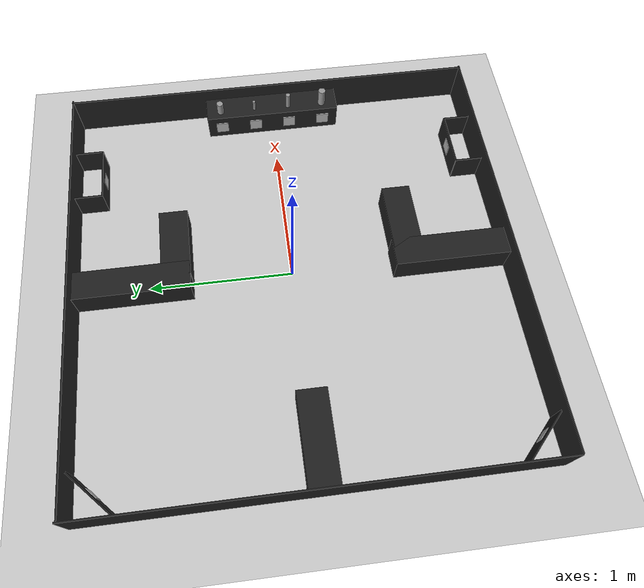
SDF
<sdf version='1.4'>
  <world name='default'>
    <!-- A global light source -->
    <include>
      <uri>model://sun</uri>
    </include>

    <!-- A ground plane -->
    <include>
      <uri>model://ground_plane</uri>
    </include>

    <physics type="ode">
      <real_time_update_rate>1000.0</real_time_update_rate>
      <max_step_size>0.001</max_step_size>
      <real_time_factor>1</real_time_factor>
      <ode>
        <solver>
          <type>quick</type>
          <iters>150</iters>
          <precon_iters>0</precon_iters>
          <sor>1.400000</sor>
          <use_dynamic_moi_rescaling>1</use_dynamic_moi_rescaling>
        </solver>
        <constraints>
          <cfm>0.00001</cfm>
          <erp>0.2</erp>
          <contact_max_correcting_vel>2000.000000</contact_max_correcting_vel>
          <contact_surface_layer>0.01000</contact_surface_layer>
        </constraints>
      </ode>
    </physics>

    <!-- Load world -->

    <include>
      <pose>0 0 0 0 0 -1.57</pose>
      <uri>model://turtlebot3_home_service/course</uri>
    </include>

    <include>
      <pose frame=''>1.285 0.39 0.1 0 0 1.57</pose>
      <uri>model://turtlebot3_home_service/armarker00</uri>
    </include>

    <include>
      <pose frame=''>1.285 0.13 0.1 0 0 1.57</pose>
      <uri>model://turtlebot3_home_service/armarker01</uri>
    </include>

    <include>
      <pose frame=''>1.285 -0.13 0.1 0 0 1.57</pose>
      <uri>model://turtlebot3_home_service/armarker02</uri>
    </include>

    <include>
      <pose frame=''>1.285 -0.39 0.1 0 0 1.57</pose>
      <uri>model://turtlebot3_home_service/armarker03</uri>
    </include>

    <include>
      <pose frame=''>1.35 0.39 0.2 0 0 0</pose>
      <uri>model://turtlebot3_home_service/object0</uri>
    </include>

    <include>
      <pose frame=''>1.35 0.13 0.2 0 0 0</pose>
      <uri>model://turtlebot3_home_service/object1</uri>
    </include>

    <include>
      <pose frame=''>1.35 -0.13 0.2 0 0 0</pose>
      <uri>model://turtlebot3_home_service/object2</uri>
    </include>

    <include>
      <pose frame=''>1.35 -0.39 0.2 0 0 0</pose>
      <uri>model://turtlebot3_home_service/object3</uri>
    </include>

    <light name='user_directional_light_0' type='directional'>
      <pose frame=''>-4.454953 0.018698 1.796531 0 -1.344354 0</pose>
      <diffuse>0.5 0.5 0.5 1</diffuse>
      <specular>0.1 0.1 0.1 1</specular>
      <direction>0.1 0.1 -0.9</direction>
      <attenuation>
        <range>20</range>
        <constant>0.5</constant>
        <linear>0.01</linear>
        <quadratic>0.001</quadratic>
      </attenuation>
      <cast_shadows>1</cast_shadows>
    </light>

    <light name='user_directional_light_1' type='directional'>
      <pose frame=''>0.096497 2.957005 1.000000 -1.431039 -0 0</pose>
      <diffuse>0.5 0.5 0.5 1</diffuse>
      <specular>0.1 0.1 0.1 1</specular>
      <direction>0.1 0.1 -0.9</direction>
      <attenuation>
        <range>20</range>
        <constant>0.5</constant>
        <linear>0.01</linear>
        <quadratic>0.001</quadratic>
      </attenuation>
      <cast_shadows>1</cast_shadows>
    </light>

    <scene>
      <ambient>0.4 0.4 0.4 1</ambient>
      <background>0.7 0.7 0.7 1</background>
      <shadows>true</shadows>
    </scene>

    <gui fullscreen='0'>
      <camera name='user_camera'>
        <pose>0.8 0.0 12.0 0 1.5708 0</pose>
        <view_controller>orbit</view_controller>
      </camera>
    </gui>
  </world>
</sdf>

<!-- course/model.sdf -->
<sdf version='1.6'>
  <model name='course'>
    <link name='Wall_24'>
      <pose frame=''>-1.09357 -0.012136 0 0 -0 0</pose>
      <self_collide>0</self_collide>
      <kinematic>0</kinematic>
      <visual name='Wall_24_Visual'>
        <pose frame=''>0 0 0.1 0 -0 0</pose>
        <geometry>
          <box>
            <size>0.8 0.2 0.2</size>
          </box>
        </geometry>
        <material>
          <script>
            <uri>file://media/materials/scripts/gazebo.material</uri>
            <name>Gazebo/Black</name>
          </script>
          <ambient>0 0 0 1</ambient>
          <diffuse>0.7 0.7 0.7 1</diffuse>
          <specular>0.01 0.01 0.01 1</specular>
          <emissive>0 0 0 1</emissive>
        </material>
        <cast_shadows>1</cast_shadows>
        <transparency>0</transparency>
      </visual>
      <collision name='Wall_24_Collision'>
        <laser_retro>0</laser_retro>
        <max_contacts>10</max_contacts>
        <pose frame=''>0 0 0.1 0 -0 0</pose>
        <geometry>
          <box>
            <size>0.8 0.2 0.2</size>
          </box>
        </geometry>
        <surface>
          <friction>
            <ode>
              <mu>1</mu>
              <mu2>1</mu2>
              <fdir1>0 0 0</fdir1>
              <slip1>0</slip1>
              <slip2>0</slip2>
            </ode>
            <torsional>
              <coefficient>1</coefficient>
              <patch_radius>0</patch_radius>
              <surface_radius>0</surface_radius>
              <use_patch_radius>1</use_patch_radius>
              <ode>
                <slip>0</slip>
              </ode>
            </torsional>
          </friction>
          <bounce>
            <restitution_coefficient>0</restitution_coefficient>
            <threshold>1e+06</threshold>
          </bounce>
          <contact>
            <collide_without_contact>0</collide_without_contact>
            <collide_without_contact_bitmask>1</collide_without_contact_bitmask>
            <collide_bitmask>1</collide_bitmask>
            <ode>
              <soft_cfm>0</soft_cfm>
              <soft_erp>0.2</soft_erp>
              <kp>1e+13</kp>
              <kd>1</kd>
              <max_vel>0.01</max_vel>
              <min_depth>0</min_depth>
            </ode>
            <bullet>
              <split_impulse>1</split_impulse>
              <split_impulse_penetration_threshold>-0.01</split_impulse_penetration_threshold>
              <soft_cfm>0</soft_cfm>
              <soft_erp>0.2</soft_erp>
              <kp>1e+13</kp>
              <kd>1</kd>
            </bullet>
          </contact>
        </surface>
      </collision>
    </link>
    <link name='Wall_26'>
      <pose frame=''>0.807582 0.253259 0 0 0 -1.5708</pose>
      <self_collide>0</self_collide>
      <kinematic>0</kinematic>
      <visual name='Wall_26_Visual'>
        <pose frame=''>0 0 0.1 0 -0 0</pose>
        <geometry>
          <box>
            <size>0.5 0.2 0.2</size>
          </box>
        </geometry>
        <material>
          <script>
            <uri>file://media/materials/scripts/gazebo.material</uri>
            <name>Gazebo/Black</name>
          </script>
          <ambient>0 0 0 1</ambient>
          <diffuse>0.7 0.7 0.7 1</diffuse>
          <specular>0.01 0.01 0.01 1</specular>
          <emissive>0 0 0 1</emissive>
        </material>
        <cast_shadows>1</cast_shadows>
        <transparency>0</transparency>
      </visual>
      <collision name='Wall_26_Collision'>
        <laser_retro>0</laser_retro>
        <max_contacts>10</max_contacts>
        <pose frame=''>0 0 0.1 0 -0 0</pose>
        <geometry>
          <box>
            <size>0.5 0.2 0.2</size>
          </box>
        </geometry>
        <surface>
          <friction>
            <ode>
              <mu>1</mu>
              <mu2>1</mu2>
              <fdir1>0 0 0</fdir1>
              <slip1>0</slip1>
              <slip2>0</slip2>
            </ode>
            <torsional>
              <coefficient>1</coefficient>
              <patch_radius>0</patch_radius>
              <surface_radius>0</surface_radius>
              <use_patch_radius>1</use_patch_radius>
              <ode>
                <slip>0</slip>
              </ode>
            </torsional>
          </friction>
          <bounce>
            <restitution_coefficient>0</restitution_coefficient>
            <threshold>1e+06</threshold>
          </bounce>
          <contact>
            <collide_without_contact>0</collide_without_contact>
            <collide_without_contact_bitmask>1</collide_without_contact_bitmask>
            <collide_bitmask>1</collide_bitmask>
            <ode>
              <soft_cfm>0</soft_cfm>
              <soft_erp>0.2</soft_erp>
              <kp>1e+13</kp>
              <kd>1</kd>
              <max_vel>0.01</max_vel>
              <min_depth>0</min_depth>
            </ode>
            <bullet>
              <split_impulse>1</split_impulse>
              <split_impulse_penetration_threshold>-0.01</split_impulse_penetration_threshold>
              <soft_cfm>0</soft_cfm>
              <soft_erp>0.2</soft_erp>
              <kp>1e+13</kp>
              <kd>1</kd>
            </bullet>
          </contact>
        </surface>
      </collision>
    </link>
    <link name='Wall_29'>
      <pose frame=''>1.09953 -0.015043 0 0 -0 3.14159</pose>
      <self_collide>0</self_collide>
      <kinematic>0</kinematic>
      <visual name='Wall_29_Visual'>
        <pose frame=''>0 0 0.1 0 -0 0</pose>
        <geometry>
          <box>
            <size>0.8 0.2 0.2</size>
          </box>
        </geometry>
        <material>
          <script>
            <uri>file://media/materials/scripts/gazebo.material</uri>
            <name>Gazebo/Black</name>
          </script>
          <ambient>0 0 0 1</ambient>
          <diffuse>0.7 0.7 0.7 1</diffuse>
          <specular>0.01 0.01 0.01 1</specular>
          <emissive>0 0 0 1</emissive>
        </material>
        <cast_shadows>1</cast_shadows>
        <transparency>0</transparency>
      </visual>
      <collision name='Wall_29_Collision'>
        <laser_retro>0</laser_retro>
        <max_contacts>10</max_contacts>
        <pose frame=''>0 0 0.1 0 -0 0</pose>
        <geometry>
          <box>
            <size>0.8 0.2 0.2</size>
          </box>
        </geometry>
        <surface>
          <friction>
            <ode>
              <mu>1</mu>
              <mu2>1</mu2>
              <fdir1>0 0 0</fdir1>
              <slip1>0</slip1>
              <slip2>0</slip2>
            </ode>
            <torsional>
              <coefficient>1</coefficient>
              <patch_radius>0</patch_radius>
              <surface_radius>0</surface_radius>
              <use_patch_radius>1</use_patch_radius>
              <ode>
                <slip>0</slip>
              </ode>
            </torsional>
          </friction>
          <bounce>
            <restitution_coefficient>0</restitution_coefficient>
            <threshold>1e+06</threshold>
          </bounce>
          <contact>
            <collide_without_contact>0</collide_without_contact>
            <collide_without_contact_bitmask>1</collide_without_contact_bitmask>
            <collide_bitmask>1</collide_bitmask>
            <ode>
              <soft_cfm>0</soft_cfm>
              <soft_erp>0.2</soft_erp>
              <kp>1e+13</kp>
              <kd>1</kd>
              <max_vel>0.01</max_vel>
              <min_depth>0</min_depth>
            </ode>
            <bullet>
              <split_impulse>1</split_impulse>
              <split_impulse_penetration_threshold>-0.01</split_impulse_penetration_threshold>
              <soft_cfm>0</soft_cfm>
              <soft_erp>0.2</soft_erp>
              <kp>1e+13</kp>
              <kd>1</kd>
            </bullet>
          </contact>
        </surface>
      </collision>
    </link>
    <link name='Wall_31'>
      <pose frame=''>-0.789418 0.239259 0 0 -0 1.5708</pose>
      <self_collide>0</self_collide>
      <kinematic>0</kinematic>
      <visual name='Wall_31_Visual'>
        <pose frame=''>0 0 0.1 0 -0 0</pose>
        <geometry>
          <box>
            <size>0.5 0.2 0.2</size>
          </box>
        </geometry>
        <material>
          <script>
            <uri>file://media/materials/scripts/gazebo.material</uri>
            <name>Gazebo/Black</name>
          </script>
          <ambient>0 0 0 1</ambient>
          <diffuse>0.7 0.7 0.7 1</diffuse>
          <specular>0.01 0.01 0.01 1</specular>
          <emissive>0 0 0 1</emissive>
        </material>
        <cast_shadows>1</cast_shadows>
        <transparency>0</transparency>
      </visual>
      <collision name='Wall_31_Collision'>
        <laser_retro>0</laser_retro>
        <max_contacts>10</max_contacts>
        <pose frame=''>0 0 0.1 0 -0 0</pose>
        <geometry>
          <box>
            <size>0.5 0.2 0.2</size>
          </box>
        </geometry>
        <surface>
          <friction>
            <ode>
              <mu>1</mu>
              <mu2>1</mu2>
              <fdir1>0 0 0</fdir1>
              <slip1>0</slip1>
              <slip2>0</slip2>
            </ode>
            <torsional>
              <coefficient>1</coefficient>
              <patch_radius>0</patch_radius>
              <surface_radius>0</surface_radius>
              <use_patch_radius>1</use_patch_radius>
              <ode>
                <slip>0</slip>
              </ode>
            </torsional>
          </friction>
          <bounce>
            <restitution_coefficient>0</restitution_coefficient>
            <threshold>1e+06</threshold>
          </bounce>
          <contact>
            <collide_without_contact>0</collide_without_contact>
            <collide_without_contact_bitmask>1</collide_without_contact_bitmask>
            <collide_bitmask>1</collide_bitmask>
            <ode>
              <soft_cfm>0</soft_cfm>
              <soft_erp>0.2</soft_erp>
              <kp>1e+13</kp>
              <kd>1</kd>
              <max_vel>0.01</max_vel>
              <min_depth>0</min_depth>
            </ode>
            <bullet>
              <split_impulse>1</split_impulse>
              <split_impulse_penetration_threshold>-0.01</split_impulse_penetration_threshold>
              <soft_cfm>0</soft_cfm>
              <soft_erp>0.2</soft_erp>
              <kp>1e+13</kp>
              <kd>1</kd>
            </bullet>
          </contact>
        </surface>
      </collision>
    </link>
    <link name='Wall_33'>
      <pose frame=''>0.00734 -1.1961 0 0 -0 1.5708</pose>
      <self_collide>0</self_collide>
      <kinematic>0</kinematic>
      <visual name='Wall_33_Visual'>
        <pose frame=''>0 0 0.1 0 -0 0</pose>
        <geometry>
          <box>
            <size>0.6 0.2 0.2</size>
          </box>
        </geometry>
        <material>
          <script>
            <uri>file://media/materials/scripts/gazebo.material</uri>
            <name>Gazebo/Black</name>
          </script>
          <ambient>0 0 0 1</ambient>
          <diffuse>0.7 0.7 0.7 1</diffuse>
          <specular>0.01 0.01 0.01 1</specular>
          <emissive>0 0 0 1</emissive>
        </material>
        <cast_shadows>1</cast_shadows>
        <transparency>0</transparency>
      </visual>
      <collision name='Wall_33_Collision'>
        <laser_retro>0</laser_retro>
        <max_contacts>10</max_contacts>
        <pose frame=''>0 0 0.1 0 -0 0</pose>
        <geometry>
          <box>
            <size>0.6 0.2 0.2</size>
          </box>
        </geometry>
        <surface>
          <friction>
            <ode>
              <mu>1</mu>
              <mu2>1</mu2>
              <fdir1>0 0 0</fdir1>
              <slip1>0</slip1>
              <slip2>0</slip2>
            </ode>
            <torsional>
              <coefficient>1</coefficient>
              <patch_radius>0</patch_radius>
              <surface_radius>0</surface_radius>
              <use_patch_radius>1</use_patch_radius>
              <ode>
                <slip>0</slip>
              </ode>
            </torsional>
          </friction>
          <bounce>
            <restitution_coefficient>0</restitution_coefficient>
            <threshold>1e+06</threshold>
          </bounce>
          <contact>
            <collide_without_contact>0</collide_without_contact>
            <collide_without_contact_bitmask>1</collide_without_contact_bitmask>
            <collide_bitmask>1</collide_bitmask>
            <ode>
              <soft_cfm>0</soft_cfm>
              <soft_erp>0.2</soft_erp>
              <kp>1e+13</kp>
              <kd>1</kd>
              <max_vel>0.01</max_vel>
              <min_depth>0</min_depth>
            </ode>
            <bullet>
              <split_impulse>1</split_impulse>
              <split_impulse_penetration_threshold>-0.01</split_impulse_penetration_threshold>
              <soft_cfm>0</soft_cfm>
              <soft_erp>0.2</soft_erp>
              <kp>1e+13</kp>
              <kd>1</kd>
            </bullet>
          </contact>
        </surface>
      </collision>
    </link>
    <link name='Wall_35'>
      <pose frame=''>0.004067 1.38776 0 0 -0 3.14159</pose>
      <self_collide>0</self_collide>
      <kinematic>0</kinematic>
      <visual name='Wall_35_Visual'>
        <pose frame=''>0 0 0.1 0 -0 0</pose>
        <geometry>
          <box>
            <size>1 0.2 0.2</size>
          </box>
        </geometry>
        <material>
          <script>
            <uri>file://media/materials/scripts/gazebo.material</uri>
            <name>Gazebo/Black</name>
          </script>
          <ambient>0 0 0 1</ambient>
          <diffuse>0.7 0.7 0.7 1</diffuse>
          <specular>0.01 0.01 0.01 1</specular>
          <emissive>0 0 0 1</emissive>
        </material>
        <cast_shadows>1</cast_shadows>
        <transparency>0</transparency>
      </visual>
      <collision name='Wall_35_Collision'>
        <laser_retro>0</laser_retro>
        <max_contacts>10</max_contacts>
        <pose frame=''>0 0 0.1 0 -0 0</pose>
        <geometry>
          <box>
            <size>1 0.2 0.2</size>
          </box>
        </geometry>
        <surface>
          <friction>
            <ode>
              <mu>1</mu>
              <mu2>1</mu2>
              <fdir1>0 0 0</fdir1>
              <slip1>0</slip1>
              <slip2>0</slip2>
            </ode>
            <torsional>
              <coefficient>1</coefficient>
              <patch_radius>0</patch_radius>
              <surface_radius>0</surface_radius>
              <use_patch_radius>1</use_patch_radius>
              <ode>
                <slip>0</slip>
              </ode>
            </torsional>
          </friction>
          <bounce>
            <restitution_coefficient>0</restitution_coefficient>
            <threshold>1e+06</threshold>
          </bounce>
          <contact>
            <collide_without_contact>0</collide_without_contact>
            <collide_without_contact_bitmask>1</collide_without_contact_bitmask>
            <collide_bitmask>1</collide_bitmask>
            <ode>
              <soft_cfm>0</soft_cfm>
              <soft_erp>0.2</soft_erp>
              <kp>1e+13</kp>
              <kd>1</kd>
              <max_vel>0.01</max_vel>
              <min_depth>0</min_depth>
            </ode>
            <bullet>
              <split_impulse>1</split_impulse>
              <split_impulse_penetration_threshold>-0.01</split_impulse_penetration_threshold>
              <soft_cfm>0</soft_cfm>
              <soft_erp>0.2</soft_erp>
              <kp>1e+13</kp>
              <kd>1</kd>
            </bullet>
          </contact>
        </surface>
      </collision>
    </link>
    <link name='Wall_41'>
      <pose frame=''>-1.28765 0.883978 0 0 -0 1.5708</pose>
      <self_collide>0</self_collide>
      <kinematic>0</kinematic>
      <visual name='Wall_41_Visual'>
        <pose frame=''>0 0 0.1 0 -0 0</pose>
        <geometry>
          <box>
            <size>0.4 0.01 0.2</size>
          </box>
        </geometry>
        <material>
          <script>
            <uri>file://media/materials/scripts/gazebo.material</uri>
            <name>Gazebo/Black</name>
          </script>
          <ambient>0 0 0 1</ambient>
          <diffuse>0.7 0.7 0.7 1</diffuse>
          <specular>0.01 0.01 0.01 1</specular>
          <emissive>0 0 0 1</emissive>
        </material>
        <cast_shadows>1</cast_shadows>
        <transparency>0</transparency>
      </visual>
      <collision name='Wall_41_Collision'>
        <laser_retro>0</laser_retro>
        <max_contacts>10</max_contacts>
        <pose frame=''>0 0 0.1 0 -0 0</pose>
        <geometry>
          <box>
            <size>0.4 0.01 0.2</size>
          </box>
        </geometry>
        <surface>
          <friction>
            <ode>
              <mu>1</mu>
              <mu2>1</mu2>
              <fdir1>0 0 0</fdir1>
              <slip1>0</slip1>
              <slip2>0</slip2>
            </ode>
            <torsional>
              <coefficient>1</coefficient>
              <patch_radius>0</patch_radius>
              <surface_radius>0</surface_radius>
              <use_patch_radius>1</use_patch_radius>
              <ode>
                <slip>0</slip>
              </ode>
            </torsional>
          </friction>
          <bounce>
            <restitution_coefficient>0</restitution_coefficient>
            <threshold>1e+06</threshold>
          </bounce>
          <contact>
            <collide_without_contact>0</collide_without_contact>
            <collide_without_contact_bitmask>1</collide_without_contact_bitmask>
            <collide_bitmask>1</collide_bitmask>
            <ode>
              <soft_cfm>0</soft_cfm>
              <soft_erp>0.2</soft_erp>
              <kp>1e+13</kp>
              <kd>1</kd>
              <max_vel>0.01</max_vel>
              <min_depth>0</min_depth>
            </ode>
            <bullet>
              <split_impulse>1</split_impulse>
              <split_impulse_penetration_threshold>-0.01</split_impulse_penetration_threshold>
              <soft_cfm>0</soft_cfm>
              <soft_erp>0.2</soft_erp>
              <kp>1e+13</kp>
              <kd>1</kd>
            </bullet>
          </contact>
        </surface>
      </collision>
    </link>
    <link name='Wall_41_clone'>
      <pose frame=''>1.30078 0.8837 0 0 -0 -1.57381</pose>
      <self_collide>0</self_collide>
      <kinematic>0</kinematic>
      <visual name='Wall_41_Visual'>
        <pose frame=''>0 0 0.1 0 -0 0</pose>
        <geometry>
          <box>
            <size>0.4 0.01 0.2</size>
          </box>
        </geometry>
        <material>
          <script>
            <uri>file://media/materials/scripts/gazebo.material</uri>
            <name>Gazebo/Black</name>
          </script>
          <ambient>0 0 0 1</ambient>
          <diffuse>0.7 0.7 0.7 1</diffuse>
          <specular>0.01 0.01 0.01 1</specular>
          <emissive>0 0 0 1</emissive>
          <shader type='pixel'/>
        </material>
        <cast_shadows>1</cast_shadows>
        <transparency>0</transparency>
      </visual>
      <collision name='Wall_41_Collision'>
        <laser_retro>0</laser_retro>
        <max_contacts>10</max_contacts>
        <pose frame=''>0 0 0.1 0 -0 0</pose>
        <geometry>
          <box>
            <size>0.4 0.01 0.2</size>
          </box>
        </geometry>
        <surface>
          <friction>
            <ode>
              <mu>1</mu>
              <mu2>1</mu2>
              <fdir1>0 0 0</fdir1>
              <slip1>0</slip1>
              <slip2>0</slip2>
            </ode>
            <torsional>
              <coefficient>1</coefficient>
              <patch_radius>0</patch_radius>
              <surface_radius>0</surface_radius>
              <use_patch_radius>1</use_patch_radius>
              <ode>
                <slip>0</slip>
              </ode>
            </torsional>
          </friction>
          <bounce>
            <restitution_coefficient>0</restitution_coefficient>
            <threshold>1e+06</threshold>
          </bounce>
          <contact>
            <collide_without_contact>0</collide_without_contact>
            <collide_without_contact_bitmask>1</collide_without_contact_bitmask>
            <collide_bitmask>1</collide_bitmask>
            <ode>
              <soft_cfm>0</soft_cfm>
              <soft_erp>0.2</soft_erp>
              <kp>1e+13</kp>
              <kd>1</kd>
              <max_vel>0.01</max_vel>
              <min_depth>0</min_depth>
            </ode>
            <bullet>
              <split_impulse>1</split_impulse>
              <split_impulse_penetration_threshold>-0.01</split_impulse_penetration_threshold>
              <soft_cfm>0</soft_cfm>
              <soft_erp>0.2</soft_erp>
              <kp>1e+13</kp>
              <kd>1</kd>
            </bullet>
          </contact>
        </surface>
      </collision>
    </link>
    <link name='Wall_43'>
      <pose frame=''>-1.38265 0.688978 0 0 -0 3.14159</pose>
      <self_collide>0</self_collide>
      <kinematic>0</kinematic>
      <visual name='Wall_43_Visual'>
        <pose frame=''>0 0 0.1 0 -0 0</pose>
        <geometry>
          <box>
            <size>0.2 0.01 0.2</size>
          </box>
        </geometry>
        <material>
          <script>
            <uri>file://media/materials/scripts/gazebo.material</uri>
            <name>Gazebo/Black</name>
          </script>
          <ambient>0 0 0 1</ambient>
          <diffuse>0.7 0.7 0.7 1</diffuse>
          <specular>0.01 0.01 0.01 1</specular>
          <emissive>0 0 0 1</emissive>
        </material>
        <cast_shadows>1</cast_shadows>
        <transparency>0</transparency>
      </visual>
      <collision name='Wall_43_Collision'>
        <laser_retro>0</laser_retro>
        <max_contacts>10</max_contacts>
        <pose frame=''>0 0 0.1 0 -0 0</pose>
        <geometry>
          <box>
            <size>0.2 0.01 0.2</size>
          </box>
        </geometry>
        <surface>
          <friction>
            <ode>
              <mu>1</mu>
              <mu2>1</mu2>
              <fdir1>0 0 0</fdir1>
              <slip1>0</slip1>
              <slip2>0</slip2>
            </ode>
            <torsional>
              <coefficient>1</coefficient>
              <patch_radius>0</patch_radius>
              <surface_radius>0</surface_radius>
              <use_patch_radius>1</use_patch_radius>
              <ode>
                <slip>0</slip>
              </ode>
            </torsional>
          </friction>
          <bounce>
            <restitution_coefficient>0</restitution_coefficient>
            <threshold>1e+06</threshold>
          </bounce>
          <contact>
            <collide_without_contact>0</collide_without_contact>
            <collide_without_contact_bitmask>1</collide_without_contact_bitmask>
            <collide_bitmask>1</collide_bitmask>
            <ode>
              <soft_cfm>0</soft_cfm>
              <soft_erp>0.2</soft_erp>
              <kp>1e+13</kp>
              <kd>1</kd>
              <max_vel>0.01</max_vel>
              <min_depth>0</min_depth>
            </ode>
            <bullet>
              <split_impulse>1</split_impulse>
              <split_impulse_penetration_threshold>-0.01</split_impulse_penetration_threshold>
              <soft_cfm>0</soft_cfm>
              <soft_erp>0.2</soft_erp>
              <kp>1e+13</kp>
              <kd>1</kd>
            </bullet>
          </contact>
        </surface>
      </collision>
    </link>
    <link name='Wall_45'>
      <pose frame=''>-1.38265 1.07898 0 0 -0 3.14159</pose>
      <self_collide>0</self_collide>
      <kinematic>0</kinematic>
      <visual name='Wall_45_Visual'>
        <pose frame=''>0 0 0.1 0 -0 0</pose>
        <geometry>
          <box>
            <size>0.2 0.01 0.2</size>
          </box>
        </geometry>
        <material>
          <script>
            <uri>file://media/materials/scripts/gazebo.material</uri>
            <name>Gazebo/Black</name>
          </script>
          <ambient>0 0 0 1</ambient>
          <diffuse>0.7 0.7 0.7 1</diffuse>
          <specular>0.01 0.01 0.01 1</specular>
          <emissive>0 0 0 1</emissive>
        </material>
        <cast_shadows>1</cast_shadows>
        <transparency>0</transparency>
      </visual>
      <collision name='Wall_45_Collision'>
        <laser_retro>0</laser_retro>
        <max_contacts>10</max_contacts>
        <pose frame=''>0 0 0.1 0 -0 0</pose>
        <geometry>
          <box>
            <size>0.2 0.01 0.2</size>
          </box>
        </geometry>
        <surface>
          <friction>
            <ode>
              <mu>1</mu>
              <mu2>1</mu2>
              <fdir1>0 0 0</fdir1>
              <slip1>0</slip1>
              <slip2>0</slip2>
            </ode>
            <torsional>
              <coefficient>1</coefficient>
              <patch_radius>0</patch_radius>
              <surface_radius>0</surface_radius>
              <use_patch_radius>1</use_patch_radius>
              <ode>
                <slip>0</slip>
              </ode>
            </torsional>
          </friction>
          <bounce>
            <restitution_coefficient>0</restitution_coefficient>
            <threshold>1e+06</threshold>
          </bounce>
          <contact>
            <collide_without_contact>0</collide_without_contact>
            <collide_without_contact_bitmask>1</collide_without_contact_bitmask>
            <collide_bitmask>1</collide_bitmask>
            <ode>
              <soft_cfm>0</soft_cfm>
              <soft_erp>0.2</soft_erp>
              <kp>1e+13</kp>
              <kd>1</kd>
              <max_vel>0.01</max_vel>
              <min_depth>0</min_depth>
            </ode>
            <bullet>
              <split_impulse>1</split_impulse>
              <split_impulse_penetration_threshold>-0.01</split_impulse_penetration_threshold>
              <soft_cfm>0</soft_cfm>
              <soft_erp>0.2</soft_erp>
              <kp>1e+13</kp>
              <kd>1</kd>
            </bullet>
          </contact>
        </surface>
      </collision>
    </link>
    <link name='Wall_54'>
      <pose frame=''>1.39817 0.684198 0 0 -0 0</pose>
      <self_collide>0</self_collide>
      <kinematic>0</kinematic>
      <visual name='Wall_54_Visual'>
        <pose frame=''>0 0 0.1 0 -0 0</pose>
        <geometry>
          <box>
            <size>0.2 0.01 0.2</size>
          </box>
        </geometry>
        <material>
          <script>
            <uri>file://media/materials/scripts/gazebo.material</uri>
            <name>Gazebo/Black</name>
          </script>
          <ambient>0 0 0 1</ambient>
          <diffuse>0.7 0.7 0.7 1</diffuse>
          <specular>0.01 0.01 0.01 1</specular>
          <emissive>0 0 0 1</emissive>
        </material>
        <cast_shadows>1</cast_shadows>
        <transparency>0</transparency>
      </visual>
      <collision name='Wall_54_Collision'>
        <laser_retro>0</laser_retro>
        <max_contacts>10</max_contacts>
        <pose frame=''>0 0 0.1 0 -0 0</pose>
        <geometry>
          <box>
            <size>0.2 0.01 0.2</size>
          </box>
        </geometry>
        <surface>
          <friction>
            <ode>
              <mu>1</mu>
              <mu2>1</mu2>
              <fdir1>0 0 0</fdir1>
              <slip1>0</slip1>
              <slip2>0</slip2>
            </ode>
            <torsional>
              <coefficient>1</coefficient>
              <patch_radius>0</patch_radius>
              <surface_radius>0</surface_radius>
              <use_patch_radius>1</use_patch_radius>
              <ode>
                <slip>0</slip>
              </ode>
            </torsional>
          </friction>
          <bounce>
            <restitution_coefficient>0</restitution_coefficient>
            <threshold>1e+06</threshold>
          </bounce>
          <contact>
            <collide_without_contact>0</collide_without_contact>
            <collide_without_contact_bitmask>1</collide_without_contact_bitmask>
            <collide_bitmask>1</collide_bitmask>
            <ode>
              <soft_cfm>0</soft_cfm>
              <soft_erp>0.2</soft_erp>
              <kp>1e+13</kp>
              <kd>1</kd>
              <max_vel>0.01</max_vel>
              <min_depth>0</min_depth>
            </ode>
            <bullet>
              <split_impulse>1</split_impulse>
              <split_impulse_penetration_threshold>-0.01</split_impulse_penetration_threshold>
              <soft_cfm>0</soft_cfm>
              <soft_erp>0.2</soft_erp>
              <kp>1e+13</kp>
              <kd>1</kd>
            </bullet>
          </contact>
        </surface>
      </collision>
    </link>
    <link name='Wall_54_clone'>
      <pose frame=''>1.40626 1.07936 0 0 0 -0.001318</pose>
      <self_collide>0</self_collide>
      <kinematic>0</kinematic>
      <visual name='Wall_54_Visual'>
        <pose frame=''>0 0 0.1 0 -0 0</pose>
        <geometry>
          <box>
            <size>0.2 0.01 0.2</size>
          </box>
        </geometry>
        <material>
          <script>
            <uri>file://media/materials/scripts/gazebo.material</uri>
            <name>Gazebo/Black</name>
          </script>
          <ambient>0 0 0 1</ambient>
          <diffuse>0.7 0.7 0.7 1</diffuse>
          <specular>0.01 0.01 0.01 1</specular>
          <emissive>0 0 0 1</emissive>
          <shader type='pixel'/>
        </material>
        <cast_shadows>1</cast_shadows>
        <transparency>0</transparency>
      </visual>
      <collision name='Wall_54_Collision'>
        <laser_retro>0</laser_retro>
        <max_contacts>10</max_contacts>
        <pose frame=''>0 0 0.1 0 -0 0</pose>
        <geometry>
          <box>
            <size>0.2 0.01 0.2</size>
          </box>
        </geometry>
        <surface>
          <friction>
            <ode>
              <mu>1</mu>
              <mu2>1</mu2>
              <fdir1>0 0 0</fdir1>
              <slip1>0</slip1>
              <slip2>0</slip2>
            </ode>
            <torsional>
              <coefficient>1</coefficient>
              <patch_radius>0</patch_radius>
              <surface_radius>0</surface_radius>
              <use_patch_radius>1</use_patch_radius>
              <ode>
                <slip>0</slip>
              </ode>
            </torsional>
          </friction>
          <bounce>
            <restitution_coefficient>0</restitution_coefficient>
            <threshold>1e+06</threshold>
          </bounce>
          <contact>
            <collide_without_contact>0</collide_without_contact>
            <collide_without_contact_bitmask>1</collide_without_contact_bitmask>
            <collide_bitmask>1</collide_bitmask>
            <ode>
              <soft_cfm>0</soft_cfm>
              <soft_erp>0.2</soft_erp>
              <kp>1e+13</kp>
              <kd>1</kd>
              <max_vel>0.01</max_vel>
              <min_depth>0</min_depth>
            </ode>
            <bullet>
              <split_impulse>1</split_impulse>
              <split_impulse_penetration_threshold>-0.01</split_impulse_penetration_threshold>
              <soft_cfm>0</soft_cfm>
              <soft_erp>0.2</soft_erp>
              <kp>1e+13</kp>
              <kd>1</kd>
            </bullet>
          </contact>
        </surface>
      </collision>
    </link>
    <link name='Wall_56'>
      <pose frame=''>-1.33997 -1.35548 0 0 0 -0.785398</pose>
      <self_collide>0</self_collide>
      <kinematic>0</kinematic>
      <visual name='Wall_56_Visual'>
        <pose frame=''>0 0 0.1 0 -0 0</pose>
        <geometry>
          <box>
            <size>0.4 0.01 0.2</size>
          </box>
        </geometry>
        <material>
          <script>
            <uri>file://media/materials/scripts/gazebo.material</uri>
            <name>Gazebo/Black</name>
          </script>
          <ambient>0 0 0 1</ambient>
          <diffuse>0.7 0.7 0.7 1</diffuse>
          <specular>0.01 0.01 0.01 1</specular>
          <emissive>0 0 0 1</emissive>
        </material>
        <cast_shadows>1</cast_shadows>
        <transparency>0</transparency>
      </visual>
      <collision name='Wall_56_Collision'>
        <laser_retro>0</laser_retro>
        <max_contacts>10</max_contacts>
        <pose frame=''>0 0 0.1 0 -0 0</pose>
        <geometry>
          <box>
            <size>0.4 0.01 0.2</size>
          </box>
        </geometry>
        <surface>
          <friction>
            <ode>
              <mu>1</mu>
              <mu2>1</mu2>
              <fdir1>0 0 0</fdir1>
              <slip1>0</slip1>
              <slip2>0</slip2>
            </ode>
            <torsional>
              <coefficient>1</coefficient>
              <patch_radius>0</patch_radius>
              <surface_radius>0</surface_radius>
              <use_patch_radius>1</use_patch_radius>
              <ode>
                <slip>0</slip>
              </ode>
            </torsional>
          </friction>
          <bounce>
            <restitution_coefficient>0</restitution_coefficient>
            <threshold>1e+06</threshold>
          </bounce>
          <contact>
            <collide_without_contact>0</collide_without_contact>
            <collide_without_contact_bitmask>1</collide_without_contact_bitmask>
            <collide_bitmask>1</collide_bitmask>
            <ode>
              <soft_cfm>0</soft_cfm>
              <soft_erp>0.2</soft_erp>
              <kp>1e+13</kp>
              <kd>1</kd>
              <max_vel>0.01</max_vel>
              <min_depth>0</min_depth>
            </ode>
            <bullet>
              <split_impulse>1</split_impulse>
              <split_impulse_penetration_threshold>-0.01</split_impulse_penetration_threshold>
              <soft_cfm>0</soft_cfm>
              <soft_erp>0.2</soft_erp>
              <kp>1e+13</kp>
              <kd>1</kd>
            </bullet>
          </contact>
        </surface>
      </collision>
    </link>
    <link name='Wall_58'>
      <pose frame=''>1.35465 -1.35548 0 0 0 -2.35619</pose>
      <self_collide>0</self_collide>
      <kinematic>0</kinematic>
      <visual name='Wall_58_Visual'>
        <pose frame=''>0 0 0.1 0 -0 0</pose>
        <geometry>
          <box>
            <size>0.4 0.01 0.2</size>
          </box>
        </geometry>
        <material>
          <script>
            <uri>file://media/materials/scripts/gazebo.material</uri>
            <name>Gazebo/Black</name>
          </script>
          <ambient>0 0 0 1</ambient>
          <diffuse>0.7 0.7 0.7 1</diffuse>
          <specular>0.01 0.01 0.01 1</specular>
          <emissive>0 0 0 1</emissive>
        </material>
        <cast_shadows>1</cast_shadows>
        <transparency>0</transparency>
      </visual>
      <collision name='Wall_58_Collision'>
        <laser_retro>0</laser_retro>
        <max_contacts>10</max_contacts>
        <pose frame=''>0 0 0.1 0 -0 0</pose>
        <geometry>
          <box>
            <size>0.4 0.01 0.2</size>
          </box>
        </geometry>
        <surface>
          <friction>
            <ode>
              <mu>1</mu>
              <mu2>1</mu2>
              <fdir1>0 0 0</fdir1>
              <slip1>0</slip1>
              <slip2>0</slip2>
            </ode>
            <torsional>
              <coefficient>1</coefficient>
              <patch_radius>0</patch_radius>
              <surface_radius>0</surface_radius>
              <use_patch_radius>1</use_patch_radius>
              <ode>
                <slip>0</slip>
              </ode>
            </torsional>
          </friction>
          <bounce>
            <restitution_coefficient>0</restitution_coefficient>
            <threshold>1e+06</threshold>
          </bounce>
          <contact>
            <collide_without_contact>0</collide_without_contact>
            <collide_without_contact_bitmask>1</collide_without_contact_bitmask>
            <collide_bitmask>1</collide_bitmask>
            <ode>
              <soft_cfm>0</soft_cfm>
              <soft_erp>0.2</soft_erp>
              <kp>1e+13</kp>
              <kd>1</kd>
              <max_vel>0.01</max_vel>
              <min_depth>0</min_depth>
            </ode>
            <bullet>
              <split_impulse>1</split_impulse>
              <split_impulse_penetration_threshold>-0.01</split_impulse_penetration_threshold>
              <soft_cfm>0</soft_cfm>
              <soft_erp>0.2</soft_erp>
              <kp>1e+13</kp>
              <kd>1</kd>
            </bullet>
          </contact>
        </surface>
      </collision>
    </link>
    <link name='Wall_60'>
      <pose frame=''>-1.48907 0.005546 0 0 0 -1.5708</pose>
      <self_collide>0</self_collide>
      <kinematic>0</kinematic>
      <visual name='Wall_60_Visual'>
        <pose frame=''>0 0 0.15 0 -0 0</pose>
        <geometry>
          <box>
            <size>3 0.01 0.3</size>
          </box>
        </geometry>
        <material>
          <script>
            <uri>file://media/materials/scripts/gazebo.material</uri>
            <name>Gazebo/Black</name>
          </script>
          <ambient>0 0 0 1</ambient>
          <diffuse>0.7 0.7 0.7 1</diffuse>
          <specular>0.01 0.01 0.01 1</specular>
          <emissive>0 0 0 1</emissive>
        </material>
        <cast_shadows>1</cast_shadows>
        <transparency>0</transparency>
      </visual>
      <collision name='Wall_60_Collision'>
        <laser_retro>0</laser_retro>
        <max_contacts>10</max_contacts>
        <pose frame=''>0 0 0.15 0 -0 0</pose>
        <geometry>
          <box>
            <size>3 0.01 0.3</size>
          </box>
        </geometry>
        <surface>
          <friction>
            <ode>
              <mu>1</mu>
              <mu2>1</mu2>
              <fdir1>0 0 0</fdir1>
              <slip1>0</slip1>
              <slip2>0</slip2>
            </ode>
            <torsional>
              <coefficient>1</coefficient>
              <patch_radius>0</patch_radius>
              <surface_radius>0</surface_radius>
              <use_patch_radius>1</use_patch_radius>
              <ode>
                <slip>0</slip>
              </ode>
            </torsional>
          </friction>
          <bounce>
            <restitution_coefficient>0</restitution_coefficient>
            <threshold>1e+06</threshold>
          </bounce>
          <contact>
            <collide_without_contact>0</collide_without_contact>
            <collide_without_contact_bitmask>1</collide_without_contact_bitmask>
            <collide_bitmask>1</collide_bitmask>
            <ode>
              <soft_cfm>0</soft_cfm>
              <soft_erp>0.2</soft_erp>
              <kp>1e+13</kp>
              <kd>1</kd>
              <max_vel>0.01</max_vel>
              <min_depth>0</min_depth>
            </ode>
            <bullet>
              <split_impulse>1</split_impulse>
              <split_impulse_penetration_threshold>-0.01</split_impulse_penetration_threshold>
              <soft_cfm>0</soft_cfm>
              <soft_erp>0.2</soft_erp>
              <kp>1e+13</kp>
              <kd>1</kd>
            </bullet>
          </contact>
        </surface>
      </collision>
    </link>
    <link name='Wall_62'>
      <pose frame=''>1.49538 0.003394 0 0 0 -1.5708</pose>
      <self_collide>0</self_collide>
      <kinematic>0</kinematic>
      <visual name='Wall_62_Visual'>
        <pose frame=''>0 0 0.15 0 -0 0</pose>
        <geometry>
          <box>
            <size>3 0.01 0.3</size>
          </box>
        </geometry>
        <material>
          <script>
            <uri>file://media/materials/scripts/gazebo.material</uri>
            <name>Gazebo/Black</name>
          </script>
          <ambient>0 0 0 1</ambient>
          <diffuse>0.7 0.7 0.7 1</diffuse>
          <specular>0.01 0.01 0.01 1</specular>
          <emissive>0 0 0 1</emissive>
        </material>
        <cast_shadows>1</cast_shadows>
        <transparency>0</transparency>
      </visual>
      <collision name='Wall_62_Collision'>
        <laser_retro>0</laser_retro>
        <max_contacts>10</max_contacts>
        <pose frame=''>0 0 0.15 0 -0 0</pose>
        <geometry>
          <box>
            <size>3 0.01 0.3</size>
          </box>
        </geometry>
        <surface>
          <friction>
            <ode>
              <mu>1</mu>
              <mu2>1</mu2>
              <fdir1>0 0 0</fdir1>
              <slip1>0</slip1>
              <slip2>0</slip2>
            </ode>
            <torsional>
              <coefficient>1</coefficient>
              <patch_radius>0</patch_radius>
              <surface_radius>0</surface_radius>
              <use_patch_radius>1</use_patch_radius>
              <ode>
                <slip>0</slip>
              </ode>
            </torsional>
          </friction>
          <bounce>
            <restitution_coefficient>0</restitution_coefficient>
            <threshold>1e+06</threshold>
          </bounce>
          <contact>
            <collide_without_contact>0</collide_without_contact>
            <collide_without_contact_bitmask>1</collide_without_contact_bitmask>
            <collide_bitmask>1</collide_bitmask>
            <ode>
              <soft_cfm>0</soft_cfm>
              <soft_erp>0.2</soft_erp>
              <kp>1e+13</kp>
              <kd>1</kd>
              <max_vel>0.01</max_vel>
              <min_depth>0</min_depth>
            </ode>
            <bullet>
              <split_impulse>1</split_impulse>
              <split_impulse_penetration_threshold>-0.01</split_impulse_penetration_threshold>
              <soft_cfm>0</soft_cfm>
              <soft_erp>0.2</soft_erp>
              <kp>1e+13</kp>
              <kd>1</kd>
            </bullet>
          </contact>
        </surface>
      </collision>
    </link>
    <link name='Wall_64'>
      <pose frame=''>0.003929 1.48786 0 0 -0 0</pose>
      <self_collide>0</self_collide>
      <kinematic>0</kinematic>
      <visual name='Wall_64_Visual'>
        <pose frame=''>0 0 0.15 0 -0 0</pose>
        <geometry>
          <box>
            <size>3 0.01 0.3</size>
          </box>
        </geometry>
        <material>
          <script>
            <uri>file://media/materials/scripts/gazebo.material</uri>
            <name>Gazebo/Black</name>
          </script>
          <ambient>0 0 0 1</ambient>
          <diffuse>0.7 0.7 0.7 1</diffuse>
          <specular>0.01 0.01 0.01 1</specular>
          <emissive>0 0 0 1</emissive>
        </material>
        <cast_shadows>1</cast_shadows>
        <transparency>0</transparency>
      </visual>
      <collision name='Wall_64_Collision'>
        <laser_retro>0</laser_retro>
        <max_contacts>10</max_contacts>
        <pose frame=''>0 0 0.15 0 -0 0</pose>
        <geometry>
          <box>
            <size>3 0.01 0.3</size>
          </box>
        </geometry>
        <surface>
          <friction>
            <ode>
              <mu>1</mu>
              <mu2>1</mu2>
              <fdir1>0 0 0</fdir1>
              <slip1>0</slip1>
              <slip2>0</slip2>
            </ode>
            <torsional>
              <coefficient>1</coefficient>
              <patch_radius>0</patch_radius>
              <surface_radius>0</surface_radius>
              <use_patch_radius>1</use_patch_radius>
              <ode>
                <slip>0</slip>
              </ode>
            </torsional>
          </friction>
          <bounce>
            <restitution_coefficient>0</restitution_coefficient>
            <threshold>1e+06</threshold>
          </bounce>
          <contact>
            <collide_without_contact>0</collide_without_contact>
            <collide_without_contact_bitmask>1</collide_without_contact_bitmask>
            <collide_bitmask>1</collide_bitmask>
            <ode>
              <soft_cfm>0</soft_cfm>
              <soft_erp>0.2</soft_erp>
              <kp>1e+13</kp>
              <kd>1</kd>
              <max_vel>0.01</max_vel>
              <min_depth>0</min_depth>
            </ode>
            <bullet>
              <split_impulse>1</split_impulse>
              <split_impulse_penetration_threshold>-0.01</split_impulse_penetration_threshold>
              <soft_cfm>0</soft_cfm>
              <soft_erp>0.2</soft_erp>
              <kp>1e+13</kp>
              <kd>1</kd>
            </bullet>
          </contact>
        </surface>
      </collision>
    </link>
    <link name='Wall_66'>
      <pose frame=''>-0.003929 -1.50055 0 0 -0 0</pose>
      <self_collide>0</self_collide>
      <kinematic>0</kinematic>
      <visual name='Wall_66_Visual'>
        <pose frame=''>0 0 0.15 0 -0 0</pose>
        <geometry>
          <box>
            <size>3 0.01 0.3</size>
          </box>
        </geometry>
        <material>
          <script>
            <uri>file://media/materials/scripts/gazebo.material</uri>
            <name>Gazebo/Black</name>
          </script>
          <ambient>0 0 0 1</ambient>
          <diffuse>0.7 0.7 0.7 1</diffuse>
          <specular>0.01 0.01 0.01 1</specular>
          <emissive>0 0 0 1</emissive>
        </material>
        <cast_shadows>1</cast_shadows>
        <transparency>0</transparency>
      </visual>
      <collision name='Wall_66_Collision'>
        <laser_retro>0</laser_retro>
        <max_contacts>10</max_contacts>
        <pose frame=''>0 0 0.15 0 -0 0</pose>
        <geometry>
          <box>
            <size>3 0.01 0.3</size>
          </box>
        </geometry>
        <surface>
          <friction>
            <ode>
              <mu>1</mu>
              <mu2>1</mu2>
              <fdir1>0 0 0</fdir1>
              <slip1>0</slip1>
              <slip2>0</slip2>
            </ode>
            <torsional>
              <coefficient>1</coefficient>
              <patch_radius>0</patch_radius>
              <surface_radius>0</surface_radius>
              <use_patch_radius>1</use_patch_radius>
              <ode>
                <slip>0</slip>
              </ode>
            </torsional>
          </friction>
          <bounce>
            <restitution_coefficient>0</restitution_coefficient>
            <threshold>1e+06</threshold>
          </bounce>
          <contact>
            <collide_without_contact>0</collide_without_contact>
            <collide_without_contact_bitmask>1</collide_without_contact_bitmask>
            <collide_bitmask>1</collide_bitmask>
            <ode>
              <soft_cfm>0</soft_cfm>
              <soft_erp>0.2</soft_erp>
              <kp>1e+13</kp>
              <kd>1</kd>
              <max_vel>0.01</max_vel>
              <min_depth>0</min_depth>
            </ode>
            <bullet>
              <split_impulse>1</split_impulse>
              <split_impulse_penetration_threshold>-0.01</split_impulse_penetration_threshold>
              <soft_cfm>0</soft_cfm>
              <soft_erp>0.2</soft_erp>
              <kp>1e+13</kp>
              <kd>1</kd>
            </bullet>
          </contact>
        </surface>
      </collision>
    </link>
    <model name='armarker04'>
      <link name='link'>
        <pose frame=''>0 0 0.1 0 -0 0</pose>
        <inertial>
          <mass>1</mass>
          <inertia>
            <ixx>0.166667</ixx>
            <ixy>0</ixy>
            <ixz>0</ixz>
            <iyy>0.166667</iyy>
            <iyz>0</iyz>
            <izz>0.166667</izz>
          </inertia>
          <pose frame=''>0 0 0 0 -0 0</pose>
        </inertial>
        <self_collide>0</self_collide>
        <kinematic>0</kinematic>
        <gravity>1</gravity>
        <visual name='visual'>
          <geometry>
            <box>
              <size>0.09 0.01 0.09</size>
            </box>
          </geometry>
          <material>
            <script>
              <uri>model://turtlebot3_home_service/armarker04/materials/scripts</uri>
              <uri>model://turtlebot3_home_service/armarker04/materials/textures</uri>
              <name>armarker04</name>
            </script>
          </material>
          <pose frame=''>0 0 0 0 -0 0</pose>
          <cast_shadows>1</cast_shadows>
          <transparency>0</transparency>
        </visual>
        <collision name='collision'>
          <laser_retro>0</laser_retro>
          <max_contacts>10</max_contacts>
          <pose frame=''>0 0 0 0 -0 0</pose>
          <geometry>
            <box>
              <size>0.09 0.01 0.09</size>
            </box>
          </geometry>
          <surface>
            <friction>
              <ode>
                <mu>1</mu>
                <mu2>1</mu2>
                <fdir1>0 0 0</fdir1>
                <slip1>0</slip1>
                <slip2>0</slip2>
              </ode>
              <torsional>
                <coefficient>1</coefficient>
                <patch_radius>0</patch_radius>
                <surface_radius>0</surface_radius>
                <use_patch_radius>1</use_patch_radius>
                <ode>
                  <slip>0</slip>
                </ode>
              </torsional>
            </friction>
            <bounce>
              <restitution_coefficient>0</restitution_coefficient>
              <threshold>1e+06</threshold>
            </bounce>
            <contact>
              <collide_without_contact>0</collide_without_contact>
              <collide_without_contact_bitmask>1</collide_without_contact_bitmask>
              <collide_bitmask>1</collide_bitmask>
              <ode>
                <soft_cfm>0</soft_cfm>
                <soft_erp>0.2</soft_erp>
                <kp>1e+13</kp>
                <kd>1</kd>
                <max_vel>0.01</max_vel>
                <min_depth>0</min_depth>
              </ode>
              <bullet>
                <split_impulse>1</split_impulse>
                <split_impulse_penetration_threshold>-0.01</split_impulse_penetration_threshold>
                <soft_cfm>0</soft_cfm>
                <soft_erp>0.2</soft_erp>
                <kp>1e+13</kp>
                <kd>1</kd>
              </bullet>
            </contact>
          </surface>
        </collision>
      </link>
      <static>1</static>
      <allow_auto_disable>1</allow_auto_disable>
      <pose frame=''>-1.28501 0.880315 0 0 -0 1.5702</pose>
    </model>
    <model name='armarker05'>
      <link name='link'>
        <pose frame=''>0 0 0.1 0 -0 0</pose>
        <inertial>
          <mass>1</mass>
          <inertia>
            <ixx>0.166667</ixx>
            <ixy>0</ixy>
            <ixz>0</ixz>
            <iyy>0.166667</iyy>
            <iyz>0</iyz>
            <izz>0.166667</izz>
          </inertia>
          <pose frame=''>0 0 0 0 -0 0</pose>
        </inertial>
        <self_collide>0</self_collide>
        <kinematic>0</kinematic>
        <gravity>1</gravity>
        <visual name='visual'>
          <geometry>
            <box>
              <size>0.09 0.01 0.09</size>
            </box>
          </geometry>
          <material>
            <script>
              <uri>model://turtlebot3_home_service/armarker05/materials/scripts</uri>
              <uri>model://turtlebot3_home_service/armarker05/materials/textures</uri>
              <name>armarker05</name>
            </script>
          </material>
          <pose frame=''>0 0 0 0 -0 0</pose>
          <cast_shadows>1</cast_shadows>
          <transparency>0</transparency>
        </visual>
        <collision name='collision'>
          <laser_retro>0</laser_retro>
          <max_contacts>10</max_contacts>
          <pose frame=''>0 0 0 0 -0 0</pose>
          <geometry>
            <box>
              <size>0.09 0.01 0.09</size>
            </box>
          </geometry>
          <surface>
            <friction>
              <ode>
                <mu>1</mu>
                <mu2>1</mu2>
                <fdir1>0 0 0</fdir1>
                <slip1>0</slip1>
                <slip2>0</slip2>
              </ode>
              <torsional>
                <coefficient>1</coefficient>
                <patch_radius>0</patch_radius>
                <surface_radius>0</surface_radius>
                <use_patch_radius>1</use_patch_radius>
                <ode>
                  <slip>0</slip>
                </ode>
              </torsional>
            </friction>
            <bounce>
              <restitution_coefficient>0</restitution_coefficient>
              <threshold>1e+06</threshold>
            </bounce>
            <contact>
              <collide_without_contact>0</collide_without_contact>
              <collide_without_contact_bitmask>1</collide_without_contact_bitmask>
              <collide_bitmask>1</collide_bitmask>
              <ode>
                <soft_cfm>0</soft_cfm>
                <soft_erp>0.2</soft_erp>
                <kp>1e+13</kp>
                <kd>1</kd>
                <max_vel>0.01</max_vel>
                <min_depth>0</min_depth>
              </ode>
              <bullet>
                <split_impulse>1</split_impulse>
                <split_impulse_penetration_threshold>-0.01</split_impulse_penetration_threshold>
                <soft_cfm>0</soft_cfm>
                <soft_erp>0.2</soft_erp>
                <kp>1e+13</kp>
                <kd>1</kd>
              </bullet>
            </contact>
          </surface>
        </collision>
      </link>
      <static>1</static>
      <allow_auto_disable>1</allow_auto_disable>
      <pose frame=''>1.29531 0.887652 0 0 0 -1.57362</pose>
    </model>
    <model name='armarker06'>
      <link name='link'>
        <pose frame=''>0 0 0.1 0 -0 0</pose>
        <inertial>
          <mass>1</mass>
          <inertia>
            <ixx>0.166667</ixx>
            <ixy>0</ixy>
            <ixz>0</ixz>
            <iyy>0.166667</iyy>
            <iyz>0</iyz>
            <izz>0.166667</izz>
          </inertia>
          <pose frame=''>0 0 0 0 -0 0</pose>
        </inertial>
        <self_collide>0</self_collide>
        <kinematic>0</kinematic>
        <gravity>1</gravity>
        <visual name='visual'>
          <geometry>
            <box>
              <size>0.09 0.01 0.09</size>
            </box>
          </geometry>
          <material>
            <script>
              <uri>model://turtlebot3_home_service/armarker06/materials/scripts</uri>
              <uri>model://turtlebot3_home_service/armarker06/materials/textures</uri>
              <name>armarker06</name>
            </script>
          </material>
          <pose frame=''>0 0 0 0 -0 0</pose>
          <cast_shadows>1</cast_shadows>
          <transparency>0</transparency>
        </visual>
        <collision name='collision'>
          <laser_retro>0</laser_retro>
          <max_contacts>10</max_contacts>
          <pose frame=''>0 0 0 0 -0 0</pose>
          <geometry>
            <box>
              <size>0.09 0.01 0.09</size>
            </box>
          </geometry>
          <surface>
            <friction>
              <ode>
                <mu>1</mu>
                <mu2>1</mu2>
                <fdir1>0 0 0</fdir1>
                <slip1>0</slip1>
                <slip2>0</slip2>
              </ode>
              <torsional>
                <coefficient>1</coefficient>
                <patch_radius>0</patch_radius>
                <surface_radius>0</surface_radius>
                <use_patch_radius>1</use_patch_radius>
                <ode>
                  <slip>0</slip>
                </ode>
              </torsional>
            </friction>
            <bounce>
              <restitution_coefficient>0</restitution_coefficient>
              <threshold>1e+06</threshold>
            </bounce>
            <contact>
              <collide_without_contact>0</collide_without_contact>
              <collide_without_contact_bitmask>1</collide_without_contact_bitmask>
              <collide_bitmask>1</collide_bitmask>
              <ode>
                <soft_cfm>0</soft_cfm>
                <soft_erp>0.2</soft_erp>
                <kp>1e+13</kp>
                <kd>1</kd>
                <max_vel>0.01</max_vel>
                <min_depth>0</min_depth>
              </ode>
              <bullet>
                <split_impulse>1</split_impulse>
                <split_impulse_penetration_threshold>-0.01</split_impulse_penetration_threshold>
                <soft_cfm>0</soft_cfm>
                <soft_erp>0.2</soft_erp>
                <kp>1e+13</kp>
                <kd>1</kd>
              </bullet>
            </contact>
          </surface>
        </collision>
      </link>
      <static>1</static>
      <allow_auto_disable>1</allow_auto_disable>
      <pose frame=''>1.37165 -1.3326 0 0 -0 0.775709</pose>
    </model>
    <model name='armarker07'>
      <link name='link'>
        <pose frame=''>0 0 0.1 0 -0 0</pose>
        <inertial>
          <mass>1</mass>
          <inertia>
            <ixx>0.166667</ixx>
            <ixy>0</ixy>
            <ixz>0</ixz>
            <iyy>0.166667</iyy>
            <iyz>0</iyz>
            <izz>0.166667</izz>
          </inertia>
          <pose frame=''>0 0 0 0 -0 0</pose>
        </inertial>
        <self_collide>0</self_collide>
        <kinematic>0</kinematic>
        <gravity>1</gravity>
        <visual name='visual'>
          <geometry>
            <box>
              <size>0.09 0.01 0.09</size>
            </box>
          </geometry>
          <material>
            <script>
              <uri>model://turtlebot3_home_service/armarker07/materials/scripts</uri>
              <uri>model://turtlebot3_home_service/armarker07/materials/textures</uri>
              <name>armarker07</name>
            </script>
          </material>
          <pose frame=''>0 0 0 0 -0 0</pose>
          <cast_shadows>1</cast_shadows>
          <transparency>0</transparency>
        </visual>
        <collision name='collision'>
          <laser_retro>0</laser_retro>
          <max_contacts>10</max_contacts>
          <pose frame=''>0 0 0 0 -0 0</pose>
          <geometry>
            <box>
              <size>0.09 0.01 0.09</size>
            </box>
          </geometry>
          <surface>
            <friction>
              <ode>
                <mu>1</mu>
                <mu2>1</mu2>
                <fdir1>0 0 0</fdir1>
                <slip1>0</slip1>
                <slip2>0</slip2>
              </ode>
              <torsional>
                <coefficient>1</coefficient>
                <patch_radius>0</patch_radius>
                <surface_radius>0</surface_radius>
                <use_patch_radius>1</use_patch_radius>
                <ode>
                  <slip>0</slip>
                </ode>
              </torsional>
            </friction>
            <bounce>
              <restitution_coefficient>0</restitution_coefficient>
              <threshold>1e+06</threshold>
            </bounce>
            <contact>
              <collide_without_contact>0</collide_without_contact>
              <collide_without_contact_bitmask>1</collide_without_contact_bitmask>
              <collide_bitmask>1</collide_bitmask>
              <ode>
                <soft_cfm>0</soft_cfm>
                <soft_erp>0.2</soft_erp>
                <kp>1e+13</kp>
                <kd>1</kd>
                <max_vel>0.01</max_vel>
                <min_depth>0</min_depth>
              </ode>
              <bullet>
                <split_impulse>1</split_impulse>
                <split_impulse_penetration_threshold>-0.01</split_impulse_penetration_threshold>
                <soft_cfm>0</soft_cfm>
                <soft_erp>0.2</soft_erp>
                <kp>1e+13</kp>
                <kd>1</kd>
              </bullet>
            </contact>
          </surface>
        </collision>
      </link>
      <static>1</static>
      <allow_auto_disable>1</allow_auto_disable>
      <pose frame=''>-1.34277 -1.34416 0 0 0 -0.793213</pose>
    </model>
    <static>1</static>
    <allow_auto_disable>1</allow_auto_disable>
  </model>
</sdf>

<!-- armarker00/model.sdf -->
<sdf version='1.6'>
  <model name='armarker00'>
    <link name='link'>
      <pose frame=''>0 0 0 0 0 0</pose>
      <inertial>
        <mass>1</mass>
        <inertia>
          <ixx>0.166667</ixx>
          <ixy>0</ixy>
          <ixz>0</ixz>
          <iyy>0.166667</iyy>
          <iyz>0</iyz>
          <izz>0.166667</izz>
        </inertia>
        <pose frame=''>0 0 0 0 0 0</pose>
      </inertial>
      <self_collide>0</self_collide>
      <kinematic>0</kinematic>
      <gravity>1</gravity>
      <visual name='visual'>
        <geometry>
          <box>
            <size>0.09 0.01 0.09</size>
          </box>
        </geometry>
        <material>
          <script>
            <uri>model://turtlebot3_home_service/armarker00/materials/scripts</uri>
            <uri>model://turtlebot3_home_service/armarker00/materials/textures</uri>
            <name>armarker00</name>
          </script>
        </material>
        <pose frame=''>0 0 0 0 0 0</pose>
        <cast_shadows>1</cast_shadows>
        <transparency>0</transparency>
      </visual>
      <collision name='collision'>
        <laser_retro>0</laser_retro>
        <max_contacts>10</max_contacts>
        <pose frame=''>0 0 0 0 0 0</pose>
        <geometry>
          <box>
            <size>0.09 0.01 0.09</size>
          </box>
        </geometry>
        <surface>
          <friction>
            <ode>
              <mu>1</mu>
              <mu2>1</mu2>
              <fdir1>0 0 0</fdir1>
              <slip1>0</slip1>
              <slip2>0</slip2>
            </ode>
            <torsional>
              <coefficient>1</coefficient>
              <patch_radius>0</patch_radius>
              <surface_radius>0</surface_radius>
              <use_patch_radius>1</use_patch_radius>
              <ode>
                <slip>0</slip>
              </ode>
            </torsional>
          </friction>
          <bounce>
            <restitution_coefficient>0</restitution_coefficient>
            <threshold>1e+06</threshold>
          </bounce>
          <contact>
            <collide_without_contact>0</collide_without_contact>
            <collide_without_contact_bitmask>1</collide_without_contact_bitmask>
            <collide_bitmask>1</collide_bitmask>
            <ode>
              <soft_cfm>0</soft_cfm>
              <soft_erp>0.2</soft_erp>
              <kp>1e+13</kp>
              <kd>1</kd>
              <max_vel>0.01</max_vel>
              <min_depth>0</min_depth>
            </ode>
            <bullet>
              <split_impulse>1</split_impulse>
              <split_impulse_penetration_threshold>-0.01</split_impulse_penetration_threshold>
              <soft_cfm>0</soft_cfm>
              <soft_erp>0.2</soft_erp>
              <kp>1e+13</kp>
              <kd>1</kd>
            </bullet>
          </contact>
        </surface>
      </collision>
    </link>
    <static>1</static>
    <allow_auto_disable>1</allow_auto_disable>
  </model>
</sdf>

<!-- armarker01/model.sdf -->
<sdf version='1.6'>
  <model name='armarker01'>
    <link name='link'>
      <pose frame=''>0 0 0 0 0 0</pose>
      <inertial>
        <mass>1</mass>
        <inertia>
          <ixx>0.166667</ixx>
          <ixy>0</ixy>
          <ixz>0</ixz>
          <iyy>0.166667</iyy>
          <iyz>0</iyz>
          <izz>0.166667</izz>
        </inertia>
        <pose frame=''>0 0 0 0 0 0</pose>
      </inertial>
      <self_collide>0</self_collide>
      <kinematic>0</kinematic>
      <gravity>1</gravity>
      <visual name='visual'>
        <geometry>
          <box>
            <size>0.09 0.01 0.09</size>
          </box>
        </geometry>
        <material>
          <script>
            <uri>model://turtlebot3_home_service/armarker01/materials/scripts</uri>
            <uri>model://turtlebot3_home_service/armarker01/materials/textures</uri>
            <name>armarker01</name>
          </script>
        </material>
        <pose frame=''>0 0 0 0 0 0</pose>
        <cast_shadows>1</cast_shadows>
        <transparency>0</transparency>
      </visual>
      <collision name='collision'>
        <laser_retro>0</laser_retro>
        <max_contacts>10</max_contacts>
        <pose frame=''>0 0 0 0 -0 0</pose>
        <geometry>
          <box>
            <size>0.09 0.01 0.09</size>
          </box>
        </geometry>
        <surface>
          <friction>
            <ode>
              <mu>1</mu>
              <mu2>1</mu2>
              <fdir1>0 0 0</fdir1>
              <slip1>0</slip1>
              <slip2>0</slip2>
            </ode>
            <torsional>
              <coefficient>1</coefficient>
              <patch_radius>0</patch_radius>
              <surface_radius>0</surface_radius>
              <use_patch_radius>1</use_patch_radius>
              <ode>
                <slip>0</slip>
              </ode>
            </torsional>
          </friction>
          <bounce>
            <restitution_coefficient>0</restitution_coefficient>
            <threshold>1e+06</threshold>
          </bounce>
          <contact>
            <collide_without_contact>0</collide_without_contact>
            <collide_without_contact_bitmask>1</collide_without_contact_bitmask>
            <collide_bitmask>1</collide_bitmask>
            <ode>
              <soft_cfm>0</soft_cfm>
              <soft_erp>0.2</soft_erp>
              <kp>1e+13</kp>
              <kd>1</kd>
              <max_vel>0.01</max_vel>
              <min_depth>0</min_depth>
            </ode>
            <bullet>
              <split_impulse>1</split_impulse>
              <split_impulse_penetration_threshold>-0.01</split_impulse_penetration_threshold>
              <soft_cfm>0</soft_cfm>
              <soft_erp>0.2</soft_erp>
              <kp>1e+13</kp>
              <kd>1</kd>
            </bullet>
          </contact>
        </surface>
      </collision>
    </link>
    <static>1</static>
    <allow_auto_disable>1</allow_auto_disable>
  </model>
</sdf>

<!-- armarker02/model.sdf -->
<sdf version='1.6'>
  <model name='armarker02'>
    <link name='link'>
      <pose frame=''>0 0 0 0 0 0</pose>
      <inertial>
        <mass>1</mass>
        <inertia>
          <ixx>0.166667</ixx>
          <ixy>0</ixy>
          <ixz>0</ixz>
          <iyy>0.166667</iyy>
          <iyz>0</iyz>
          <izz>0.166667</izz>
        </inertia>
        <pose frame=''>0 0 0 0 -0 0</pose>
      </inertial>
      <self_collide>0</self_collide>
      <kinematic>0</kinematic>
      <gravity>1</gravity>
      <visual name='visual'>
        <geometry>
          <box>
            <size>0.09 0.01 0.09</size>
          </box>
        </geometry>
        <material>
          <script>
            <uri>model://turtlebot3_home_service/armarker02/materials/scripts</uri>
            <uri>model://turtlebot3_home_service/armarker02/materials/textures</uri>
            <name>armarker02</name>
          </script>
        </material>
        <pose frame=''>0 0 0 0 -0 0</pose>
        <cast_shadows>1</cast_shadows>
        <transparency>0</transparency>
      </visual>
      <collision name='collision'>
        <laser_retro>0</laser_retro>
        <max_contacts>10</max_contacts>
        <pose frame=''>0 0 0 0 -0 0</pose>
        <geometry>
          <box>
            <size>0.09 0.01 0.09</size>
          </box>
        </geometry>
        <surface>
          <friction>
            <ode>
              <mu>1</mu>
              <mu2>1</mu2>
              <fdir1>0 0 0</fdir1>
              <slip1>0</slip1>
              <slip2>0</slip2>
            </ode>
            <torsional>
              <coefficient>1</coefficient>
              <patch_radius>0</patch_radius>
              <surface_radius>0</surface_radius>
              <use_patch_radius>1</use_patch_radius>
              <ode>
                <slip>0</slip>
              </ode>
            </torsional>
          </friction>
          <bounce>
            <restitution_coefficient>0</restitution_coefficient>
            <threshold>1e+06</threshold>
          </bounce>
          <contact>
            <collide_without_contact>0</collide_without_contact>
            <collide_without_contact_bitmask>1</collide_without_contact_bitmask>
            <collide_bitmask>1</collide_bitmask>
            <ode>
              <soft_cfm>0</soft_cfm>
              <soft_erp>0.2</soft_erp>
              <kp>1e+13</kp>
              <kd>1</kd>
              <max_vel>0.01</max_vel>
              <min_depth>0</min_depth>
            </ode>
            <bullet>
              <split_impulse>1</split_impulse>
              <split_impulse_penetration_threshold>-0.01</split_impulse_penetration_threshold>
              <soft_cfm>0</soft_cfm>
              <soft_erp>0.2</soft_erp>
              <kp>1e+13</kp>
              <kd>1</kd>
            </bullet>
          </contact>
        </surface>
      </collision>
    </link>
    <static>1</static>
    <allow_auto_disable>1</allow_auto_disable>
  </model>
</sdf>

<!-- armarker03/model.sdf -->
<sdf version='1.6'>
  <model name='armarker03'>
    <link name='link'>
      <pose frame=''>0 0 0 0 0 0</pose>
      <inertial>
        <mass>1</mass>
        <inertia>
          <ixx>0.166667</ixx>
          <ixy>0</ixy>
          <ixz>0</ixz>
          <iyy>0.166667</iyy>
          <iyz>0</iyz>
          <izz>0.166667</izz>
        </inertia>
        <pose frame=''>0 0 0 0 -0 0</pose>
      </inertial>
      <self_collide>0</self_collide>
      <kinematic>0</kinematic>
      <gravity>1</gravity>
      <visual name='visual'>
        <geometry>
          <box>
            <size>0.09 0.01 0.09</size>
          </box>
        </geometry>
        <material>
          <script>
            <uri>model://turtlebot3_home_service/armarker03/materials/scripts</uri>
            <uri>model://turtlebot3_home_service/armarker03/materials/textures</uri>
            <name>armarker03</name>
          </script>
        </material>
        <pose frame=''>0 0 0 0 -0 0</pose>
        <cast_shadows>1</cast_shadows>
        <transparency>0</transparency>
      </visual>
      <collision name='collision'>
        <laser_retro>0</laser_retro>
        <max_contacts>10</max_contacts>
        <pose frame=''>0 0 0 0 -0 0</pose>
        <geometry>
          <box>
            <size>0.09 0.01 0.09</size>
          </box>
        </geometry>
        <surface>
          <friction>
            <ode>
              <mu>1</mu>
              <mu2>1</mu2>
              <fdir1>0 0 0</fdir1>
              <slip1>0</slip1>
              <slip2>0</slip2>
            </ode>
            <torsional>
              <coefficient>1</coefficient>
              <patch_radius>0</patch_radius>
              <surface_radius>0</surface_radius>
              <use_patch_radius>1</use_patch_radius>
              <ode>
                <slip>0</slip>
              </ode>
            </torsional>
          </friction>
          <bounce>
            <restitution_coefficient>0</restitution_coefficient>
            <threshold>1e+06</threshold>
          </bounce>
          <contact>
            <collide_without_contact>0</collide_without_contact>
            <collide_without_contact_bitmask>1</collide_without_contact_bitmask>
            <collide_bitmask>1</collide_bitmask>
            <ode>
              <soft_cfm>0</soft_cfm>
              <soft_erp>0.2</soft_erp>
              <kp>1e+13</kp>
              <kd>1</kd>
              <max_vel>0.01</max_vel>
              <min_depth>0</min_depth>
            </ode>
            <bullet>
              <split_impulse>1</split_impulse>
              <split_impulse_penetration_threshold>-0.01</split_impulse_penetration_threshold>
              <soft_cfm>0</soft_cfm>
              <soft_erp>0.2</soft_erp>
              <kp>1e+13</kp>
              <kd>1</kd>
            </bullet>
          </contact>
        </surface>
      </collision>
    </link>
    <static>1</static>
    <allow_auto_disable>1</allow_auto_disable>
  </model>
</sdf>

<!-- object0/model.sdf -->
<sdf version='1.6'>
  <model name='object0'>
    <link name='link_0'>
      <pose frame=''>0 0 0.0475 0 -0 0</pose>
      <inertial>
        <mass>0.010</mass>
        <inertia>
          <ixx>4.7583e-005</ixx>
          <ixy>0</ixy>
          <ixz>0</ixz>
          <iyy>4.7583e-005</iyy>
          <iyz>0</iyz>
          <izz>3.1250e-006</izz>
        </inertia>
      </inertial>
      <gravity>1</gravity>
      <self_collide>0</self_collide>
      <kinematic>0</kinematic>
      <visual name='visual'>
        <pose frame=''>0 0 0 0 -0 0</pose>
        <geometry>
          <cylinder>
            <radius>0.024</radius>
            <length>0.095</length>
          </cylinder>
        </geometry>
        <material>
          <lighting>1</lighting>
          <script>
            <uri>file://media/materials/scripts/gazebo.material</uri>
            <name>Gazebo/Grey</name>
          </script>
          <ambient>0.3 0.3 0.3 1</ambient>
          <diffuse>0.7 0.7 0.7 1</diffuse>
          <specular>0.01 0.01 0.01 1</specular>
          <emissive>0 0 0 1</emissive>
          <shader type='vertex'>
            <normal_map>__default__</normal_map>
          </shader>
        </material>
        <cast_shadows>1</cast_shadows>
        <transparency>0</transparency>
      </visual>
      <collision name='collision'>
        <laser_retro>0</laser_retro>
        <max_contacts>10</max_contacts>
        <pose frame=''>0 0 0 0 -0 0</pose>
        <geometry>
          <cylinder>
            <radius>0.024</radius>
            <length>0.095</length>
          </cylinder>
        </geometry>
        <surface>
          <friction>
            <ode>
              <mu>1000000.0</mu>
              <mu2>10000.0</mu2>
            </ode>
          </friction>
          <contact>
            <ode>
              <kp>1000000.0</kp>
              <kd>100.0</kd>
              <max_vel>1.0</max_vel>
              <min_depth>0.002</min_depth>
            </ode>
          </contact>
        </surface>
      </collision>
    </link>
    <static>0</static>
    <allow_auto_disable>1</allow_auto_disable>
  </model>
</sdf>

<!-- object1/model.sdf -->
<sdf version='1.6'>
  <model name='object1'>
    <link name='link_0'>
      <pose frame=''>0 0 0.0415 0 -0 0</pose>
      <inertial>
        <mass>0.010</mass>
        <inertia>
          <ixx>4.7583e-005</ixx>
          <ixy>0</ixy>
          <ixz>0</ixz>
          <iyy>4.7583e-005</iyy>
          <iyz>0</iyz>
          <izz>3.1250e-006</izz>
        </inertia>
      </inertial>
      <gravity>1</gravity>
      <self_collide>0</self_collide>
      <kinematic>0</kinematic>
      <visual name='visual'>
        <pose frame=''>0 0 0 0 -0 0</pose>
        <geometry>
          <cylinder>
            <radius>0.01</radius>
            <length>0.083</length>
          </cylinder>
        </geometry>
        <material>
          <lighting>1</lighting>
          <script>
            <uri>file://media/materials/scripts/gazebo.material</uri>
            <name>Gazebo/Grey</name>
          </script>
          <ambient>0.3 0.3 0.3 1</ambient>
          <diffuse>0.7 0.7 0.7 1</diffuse>
          <specular>0.01 0.01 0.01 1</specular>
          <emissive>0 0 0 1</emissive>
          <shader type='vertex'>
            <normal_map>__default__</normal_map>
          </shader>
        </material>
        <cast_shadows>1</cast_shadows>
        <transparency>0</transparency>
      </visual>
      <collision name='collision'>
        <laser_retro>0</laser_retro>
        <max_contacts>10</max_contacts>
        <pose frame=''>0 0 0 0 -0 0</pose>
        <geometry>
          <cylinder>
            <radius>0.01</radius>
            <length>0.083</length>
          </cylinder>
        </geometry>
        <surface>
          <friction>
            <ode>
              <mu>1000000.0</mu>
              <mu2>10000.0</mu2>
            </ode>
          </friction>
          <contact>
            <ode>
              <kp>1000000.0</kp>
              <kd>100.0</kd>
              <max_vel>1.0</max_vel>
              <min_depth>0.002</min_depth>
            </ode>
          </contact>
        </surface>
      </collision>
    </link>
    <static>0</static>
    <allow_auto_disable>1</allow_auto_disable>
  </model>
</sdf>

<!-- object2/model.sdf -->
<sdf version='1.6'>
  <model name='object2'>
    <link name='link_0'>
      <pose frame=''>0 0 0.061 0 -0 0</pose>
      <inertial>
        <mass>0.010</mass>
        <inertia>
          <ixx>4.7583e-005</ixx>
          <ixy>0</ixy>
          <ixz>0</ixz>
          <iyy>4.7583e-005</iyy>
          <iyz>0</iyz>
          <izz>3.1250e-006</izz>
        </inertia>
      </inertial>
      <gravity>1</gravity>
      <self_collide>0</self_collide>
      <kinematic>0</kinematic>
      <visual name='visual'>
        <pose frame=''>0 0 0 0 -0 0</pose>
        <geometry>
          <cylinder>
            <radius>0.016</radius>
            <length>0.122</length>
          </cylinder>
        </geometry>
        <material>
          <lighting>1</lighting>
          <script>
            <uri>file://media/materials/scripts/gazebo.material</uri>
            <name>Gazebo/Grey</name>
          </script>
          <ambient>0.3 0.3 0.3 1</ambient>
          <diffuse>0.7 0.7 0.7 1</diffuse>
          <specular>0.01 0.01 0.01 1</specular>
          <emissive>0 0 0 1</emissive>
          <shader type='vertex'>
            <normal_map>__default__</normal_map>
          </shader>
        </material>
        <cast_shadows>1</cast_shadows>
        <transparency>0</transparency>
      </visual>
      <collision name='collision'>
        <laser_retro>0</laser_retro>
        <max_contacts>10</max_contacts>
        <pose frame=''>0 0 0 0 -0 0</pose>
        <geometry>
          <cylinder>
            <radius>0.016</radius>
            <length>0.122</length>
          </cylinder>
        </geometry>
        <surface>
          <friction>
            <ode>
              <mu>1000000.0</mu>
              <mu2>10000.0</mu2>
            </ode>
          </friction>
          <contact>
            <ode>
              <kp>1000000.0</kp>
              <kd>100.0</kd>
              <max_vel>1.0</max_vel>
              <min_depth>0.002</min_depth>
            </ode>
          </contact>
        </surface>
      </collision>
    </link>
    <static>0</static>
    <allow_auto_disable>1</allow_auto_disable>
  </model>
</sdf>

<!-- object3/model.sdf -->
<sdf version='1.6'>
  <model name='object3'>
    <link name='link_0'>
      <pose frame=''>0 0 0.0665 0 -0 0</pose>
      <inertial>
        <mass>0.010</mass>
        <inertia>
          <ixx>4.7583e-005</ixx>
          <ixy>0</ixy>
          <ixz>0</ixz>
          <iyy>4.7583e-005</iyy>
          <iyz>0</iyz>
          <izz>3.1250e-006</izz>
        </inertia>
      </inertial>
      <gravity>1</gravity>
      <self_collide>0</self_collide>
      <kinematic>0</kinematic>
      <visual name='visual'>
        <pose frame=''>0 0 0 0 -0 0</pose>
        <geometry>
          <cylinder>
            <radius>0.026</radius>
            <length>0.133</length>
          </cylinder>
        </geometry>
        <material>
          <lighting>1</lighting>
          <script>
            <uri>file://media/materials/scripts/gazebo.material</uri>
            <name>Gazebo/Grey</name>
          </script>
          <ambient>0.3 0.3 0.3 1</ambient>
          <diffuse>0.7 0.7 0.7 1</diffuse>
          <specular>0.01 0.01 0.01 1</specular>
          <emissive>0 0 0 1</emissive>
          <shader type='vertex'>
            <normal_map>__default__</normal_map>
          </shader>
        </material>
        <cast_shadows>1</cast_shadows>
        <transparency>0</transparency>
      </visual>
      <collision name='collision'>
        <laser_retro>0</laser_retro>
        <max_contacts>10</max_contacts>
        <pose frame=''>0 0 0 0 -0 0</pose>
        <geometry>
          <cylinder>
            <radius>0.026</radius>
            <length>0.133</length>
          </cylinder>
        </geometry>
        <surface>
          <friction>
            <ode>
              <mu>1000000.0</mu>
              <mu2>10000.0</mu2>
            </ode>
          </friction>
          <contact>
            <ode>
              <kp>1000000.0</kp>
              <kd>100.0</kd>
              <max_vel>1.0</max_vel>
              <min_depth>0.002</min_depth>
            </ode>
          </contact>
        </surface>
      </collision>
    </link>
    <static>0</static>
    <allow_auto_disable>1</allow_auto_disable>
  </model>
</sdf>
